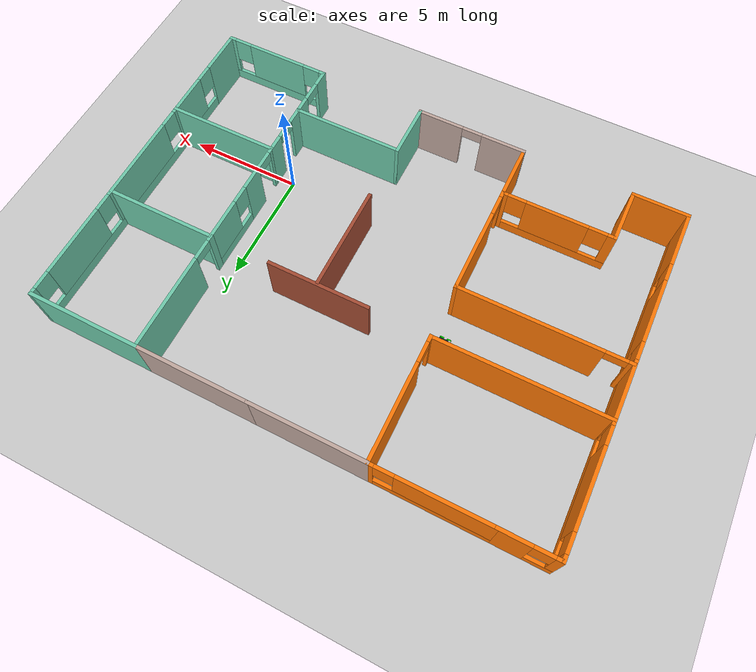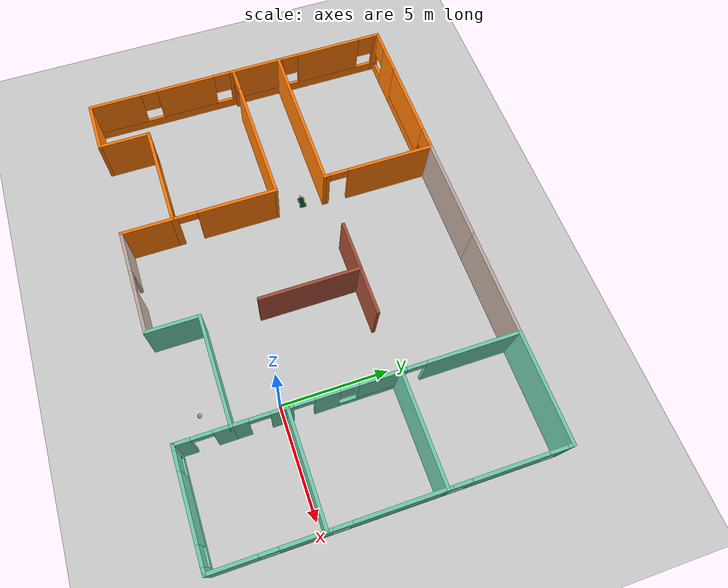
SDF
<sdf version="1.7">
 <world name="default">
  <plugin name="welcome_message" filename="libwelcome_message.so"/>
  <light name="sun" type="directional">
   <pose>0 0 10 0 -0 0</pose>
   <diffuse>0.8 0.8 0.8 1</diffuse>
   <specular>0.2 0.2 0.2 1</specular>
   <attenuation>
    <range>1000</range>
    <constant>0.9</constant>
    <linear>0.01</linear>
    <quadratic>0.001</quadratic>
   </attenuation>
   <direction>-0.5 0.1 -0.9</direction>
   <spot><inner_angle>0</inner_angle><outer_angle>0</outer_angle><falloff>0</falloff></spot>
  </light>
  <model name="ground_plane">
   <static>1</static>
   <link name="link">
    <collision name="collision">
     <geometry><plane><normal>0 0 1</normal><size>100 100</size></plane></geometry>
     <surface>
      <contact><collide_bitmask>65535</collide_bitmask></contact>
      <friction><ode><mu>100</mu><mu2>50</mu2></ode></friction>
     </surface>
    </collision>
    <visual name="visual">
     <cast_shadows>0</cast_shadows>
     <geometry><plane><normal>0 0 1</normal><size>100 100</size></plane></geometry>
     <material>
      <script><uri>file://media/materials/scripts/gazebo.material</uri><name>Gazebo/Grey</name></script>
     </material>
    </visual>
   </link>
  </model>
  <gravity>0 0 -9.8</gravity>
  <magnetic_field>6e-06 2.3e-05 -4.2e-05</magnetic_field>
  <atmosphere type="adiabatic"/>
  <physics name="default_physics" default="0" type="ode">
   <max_step_size>0.001</max_step_size>
   <real_time_factor>1</real_time_factor>
   <real_time_update_rate>1000</real_time_update_rate>
  </physics>
  <scene><ambient>0.4 0.4 0.4 1</ambient><background>0.7 0.7 0.7 1</background><shadows>1</shadows></scene>
  <spherical_coordinates>
   <surface_model>EARTH_WGS84</surface_model>
   <latitude_deg>0</latitude_deg>
   <longitude_deg>0</longitude_deg>
   <elevation>0</elevation>
   <heading_deg>0</heading_deg>
  </spherical_coordinates>
  <model name="World_1">
   <pose>-5.29578 2.9031 0 0 -0 0</pose>
   <link name="Wall_10">
    <pose>6.025 -3.9 0 0 -0 1.5708</pose>
    <visual name="Wall_10_Visual_0">
     <pose>-0.849577 0 1.25 0 -0 0</pose>
     <geometry><box><size>0.800846 0.15 2.5</size></box></geometry>
     <material>
      <script><uri>file://media/materials/scripts/gazebo.material</uri><name>Gazebo/Grey</name></script>
      <ambient>0.435294 0.796078 0.67451 1</ambient>
     </material>
     <meta><layer>0</layer></meta>
    </visual>
    <collision name="Wall_10_Collision_0">
     <geometry><box><size>0.800846 0.15 2.5</size></box></geometry>
     <pose>-0.849577 0 1.25 0 -0 0</pose>
    </collision>
    <visual name="Wall_10_Visual_1">
     <pose>0.850423 0 1.25 0 -0 0</pose>
     <geometry><box><size>0.799154 0.15 2.5</size></box></geometry>
     <material>
      <script><uri>file://media/materials/scripts/gazebo.material</uri><name>Gazebo/Grey</name></script>
      <ambient>0.435294 0.796078 0.67451 1</ambient>
     </material>
     <meta><layer>0</layer></meta>
    </visual>
    <collision name="Wall_10_Collision_1">
     <geometry><box><size>0.799154 0.15 2.5</size></box></geometry>
     <pose>0.850423 0 1.25 0 -0 0</pose>
    </collision>
    <visual name="Wall_10_Visual_2">
     <pose>0.000846 0 2.25 0 -0 0</pose>
     <geometry><box><size>0.9 0.15 0.5</size></box></geometry>
     <material>
      <script><uri>file://media/materials/scripts/gazebo.material</uri><name>Gazebo/Grey</name></script>
      <ambient>0.435294 0.796078 0.67451 1</ambient>
     </material>
     <meta><layer>0</layer></meta>
    </visual>
    <collision name="Wall_10_Collision_2">
     <geometry><box><size>0.9 0.15 0.5</size></box></geometry>
     <pose>0.000846 0 2.25 0 -0 0</pose>
    </collision>
   </link>
   <link name="Wall_11">
    <collision name="Wall_11_Collision">
     <geometry><box><size>5 0.15 2.5</size></box></geometry>
     <pose>0 0 1.25 0 -0 0</pose>
    </collision>
    <visual name="Wall_11_Visual">
     <pose>0 0 1.25 0 -0 0</pose>
     <geometry><box><size>5 0.15 2.5</size></box></geometry>
     <material>
      <script><uri>file://media/materials/scripts/gazebo.material</uri><name>Gazebo/Grey</name></script>
      <ambient>0.435294 0.796078 0.67451 1</ambient>
     </material>
     <meta><layer>0</layer></meta>
    </visual>
    <pose>8.45 -2.725 0 0 -0 0</pose>
   </link>
   <link name="Wall_13">
    <pose>6.025 -0.3 0 0 -0 1.5708</pose>
    <visual name="Wall_13_Visual_0">
     <pose>-2.34458 0 1.25 0 -0 0</pose>
     <geometry><box><size>0.310846 0.15 2.5</size></box></geometry>
     <material>
      <script><uri>file://media/materials/scripts/gazebo.material</uri><name>Gazebo/Grey</name></script>
      <ambient>0.435294 0.796078 0.67451 1</ambient>
     </material>
     <meta><layer>0</layer></meta>
    </visual>
    <collision name="Wall_13_Collision_0">
     <geometry><box><size>0.310846 0.15 2.5</size></box></geometry>
     <pose>-2.34458 0 1.25 0 -0 0</pose>
    </collision>
    <visual name="Wall_13_Visual_1">
     <pose>-0.744154 0 1.25 0 -0 0</pose>
     <geometry><box><size>1.09 0.15 2.5</size></box></geometry>
     <material>
      <script><uri>file://media/materials/scripts/gazebo.material</uri><name>Gazebo/Grey</name></script>
      <ambient>0.435294 0.796078 0.67451 1</ambient>
     </material>
     <meta><layer>0</layer></meta>
    </visual>
    <collision name="Wall_13_Collision_1">
     <geometry><box><size>1.09 0.15 2.5</size></box></geometry>
     <pose>-0.744154 0 1.25 0 -0 0</pose>
    </collision>
    <visual name="Wall_13_Visual_2">
     <pose>1.15042 0 0.25 0 -0 0</pose>
     <geometry><box><size>2.69915 0.15 0.5</size></box></geometry>
     <material>
      <script><uri>file://media/materials/scripts/gazebo.material</uri><name>Gazebo/Grey</name></script>
      <ambient>0.435294 0.796078 0.67451 1</ambient>
     </material>
     <meta><layer>0</layer></meta>
    </visual>
    <collision name="Wall_13_Collision_2">
     <geometry><box><size>2.69915 0.15 0.5</size></box></geometry>
     <pose>1.15042 0 0.25 0 -0 0</pose>
    </collision>
    <visual name="Wall_13_Visual_3">
     <pose>1.55042 0 1.5 0 -0 0</pose>
     <geometry><box><size>1.89915 0.15 2</size></box></geometry>
     <material>
      <script><uri>file://media/materials/scripts/gazebo.material</uri><name>Gazebo/Grey</name></script>
      <ambient>0.435294 0.796078 0.67451 1</ambient>
     </material>
     <meta><layer>0</layer></meta>
    </visual>
    <collision name="Wall_13_Collision_3">
     <geometry><box><size>1.89915 0.15 2</size></box></geometry>
     <pose>1.55042 0 1.5 0 -0 0</pose>
    </collision>
    <visual name="Wall_13_Visual_4">
     <pose>0.200846 0 1.9 0 -0 0</pose>
     <geometry><box><size>0.8 0.15 1.2</size></box></geometry>
     <material>
      <script><uri>file://media/materials/scripts/gazebo.material</uri><name>Gazebo/Grey</name></script>
      <ambient>0.435294 0.796078 0.67451 1</ambient>
     </material>
     <meta><layer>0</layer></meta>
    </visual>
    <collision name="Wall_13_Collision_4">
     <geometry><box><size>0.8 0.15 1.2</size></box></geometry>
     <pose>0.200846 0 1.9 0 -0 0</pose>
    </collision>
    <visual name="Wall_13_Visual_5">
     <pose>-1.73915 0 2.25 0 -0 0</pose>
     <geometry><box><size>0.9 0.15 0.5</size></box></geometry>
     <material>
      <script><uri>file://media/materials/scripts/gazebo.material</uri><name>Gazebo/Grey</name></script>
      <ambient>0.435294 0.796078 0.67451 1</ambient>
     </material>
     <meta><layer>0</layer></meta>
    </visual>
    <collision name="Wall_13_Collision_5">
     <geometry><box><size>0.9 0.15 0.5</size></box></geometry>
     <pose>-1.73915 0 2.25 0 -0 0</pose>
    </collision>
   </link>
   <link name="Wall_14">
    <collision name="Wall_14_Collision">
     <geometry><box><size>5 0.15 2.5</size></box></geometry>
     <pose>0 0 1.25 0 -0 0</pose>
    </collision>
    <visual name="Wall_14_Visual">
     <pose>0 0 1.25 0 -0 0</pose>
     <geometry><box><size>5 0.15 2.5</size></box></geometry>
     <material>
      <script><uri>file://media/materials/scripts/gazebo.material</uri><name>Gazebo/Grey</name></script>
      <ambient>0.435294 0.796078 0.67451 1</ambient>
     </material>
     <meta><layer>0</layer></meta>
    </visual>
    <pose>8.45 2.125 0 0 -0 0</pose>
   </link>
   <link name="Wall_16">
    <collision name="Wall_16_Collision">
     <geometry><box><size>5 0.15 2.5</size></box></geometry>
     <pose>0 0 1.25 0 -0 0</pose>
    </collision>
    <visual name="Wall_16_Visual">
     <pose>0 0 1.25 0 -0 0</pose>
     <geometry><box><size>5 0.15 2.5</size></box></geometry>
     <material>
      <script><uri>file://media/materials/scripts/gazebo.material</uri><name>Gazebo/Grey</name></script>
      <ambient>0.435294 0.796078 0.67451 1</ambient>
     </material>
     <meta><layer>0</layer></meta>
    </visual>
    <pose>8.45 7.425 0 0 -0 3.14159</pose>
   </link>
   <link name="Wall_17">
    <pose>6.025 4.775 0 0 0 -1.5708</pose>
    <visual name="Wall_17_Visual_0">
     <pose>-0.605423 0 1.25 0 -0 0</pose>
     <geometry><box><size>4.23915 0.15 2.5</size></box></geometry>
     <material>
      <script><uri>file://media/materials/scripts/gazebo.material</uri><name>Gazebo/Grey</name></script>
      <ambient>0.435294 0.796078 0.67451 1</ambient>
     </material>
     <meta><layer>0</layer></meta>
    </visual>
    <collision name="Wall_17_Collision_0">
     <geometry><box><size>4.23915 0.15 2.5</size></box></geometry>
     <pose>-0.605423 0 1.25 0 -0 0</pose>
    </collision>
    <visual name="Wall_17_Visual_1">
     <pose>2.56958 0 1.25 0 -0 0</pose>
     <geometry><box><size>0.310846 0.15 2.5</size></box></geometry>
     <material>
      <script><uri>file://media/materials/scripts/gazebo.material</uri><name>Gazebo/Grey</name></script>
      <ambient>0.435294 0.796078 0.67451 1</ambient>
     </material>
     <meta><layer>0</layer></meta>
    </visual>
    <collision name="Wall_17_Collision_1">
     <geometry><box><size>0.310846 0.15 2.5</size></box></geometry>
     <pose>2.56958 0 1.25 0 -0 0</pose>
    </collision>
    <visual name="Wall_17_Visual_2">
     <pose>1.96415 0 2.25 0 -0 0</pose>
     <geometry><box><size>0.9 0.15 0.5</size></box></geometry>
     <material>
      <script><uri>file://media/materials/scripts/gazebo.material</uri><name>Gazebo/Grey</name></script>
      <ambient>0.435294 0.796078 0.67451 1</ambient>
     </material>
     <meta><layer>0</layer></meta>
    </visual>
    <collision name="Wall_17_Collision_2">
     <geometry><box><size>0.9 0.15 0.5</size></box></geometry>
     <pose>1.96415 0 2.25 0 -0 0</pose>
    </collision>
   </link>
   <link name="Wall_19">
    <collision name="Wall_19_Collision">
     <geometry><box><size>2.5 0.15 2.5</size></box></geometry>
     <pose>0 0 1.25 0 -0 0</pose>
    </collision>
    <visual name="Wall_19_Visual">
     <pose>0 0 1.25 0 -0 0</pose>
     <geometry><box><size>2.5 0.15 2.5</size></box></geometry>
     <material>
      <script><uri>file://media/materials/scripts/gazebo.material</uri><name>Gazebo/Grey</name></script>
      <ambient>0.996078 0.47451 0.0196078 1</ambient>
     </material>
     <meta><layer>0</layer></meta>
    </visual>
    <pose>-3.675 -6.25 0 0 -0 1.5708</pose>
   </link>
   <link name="Wall_2">
    <pose>-1.25 -7.425 0 0 -0 0</pose>
    <visual name="Wall_2_Visual_0">
     <pose>-1.5042 0 1.25 0 -0 0</pose>
     <geometry><box><size>1.99161 0.15 2.5</size></box></geometry>
     <material>
      <script><uri>file://media/materials/scripts/gazebo.material</uri><name>Gazebo/Grey</name></script>
      <ambient>0.760784 0.662745 0.627451 1</ambient>
     </material>
     <meta><layer>0</layer></meta>
    </visual>
    <collision name="Wall_2_Collision_0">
     <geometry><box><size>1.99161 0.15 2.5</size></box></geometry>
     <pose>-1.5042 0 1.25 0 -0 0</pose>
    </collision>
    <visual name="Wall_2_Visual_1">
     <pose>1.4458 0 1.25 0 -0 0</pose>
     <geometry><box><size>2.10839 0.15 2.5</size></box></geometry>
     <material>
      <script><uri>file://media/materials/scripts/gazebo.material</uri><name>Gazebo/Grey</name></script>
      <ambient>0.760784 0.662745 0.627451 1</ambient>
     </material>
     <meta><layer>0</layer></meta>
    </visual>
    <collision name="Wall_2_Collision_1">
     <geometry><box><size>2.10839 0.15 2.5</size></box></geometry>
     <pose>1.4458 0 1.25 0 -0 0</pose>
    </collision>
    <visual name="Wall_2_Visual_2">
     <pose>-0.058393 0 2.25 0 -0 0</pose>
     <geometry><box><size>0.9 0.15 0.5</size></box></geometry>
     <material>
      <script><uri>file://media/materials/scripts/gazebo.material</uri><name>Gazebo/Grey</name></script>
      <ambient>0.760784 0.662745 0.627451 1</ambient>
     </material>
     <meta><layer>0</layer></meta>
    </visual>
    <collision name="Wall_2_Collision_2">
     <geometry><box><size>0.9 0.15 0.5</size></box></geometry>
     <pose>-0.058393 0 2.25 0 -0 0</pose>
    </collision>
   </link>
   <link name="Wall_21">
    <pose>-6.1 -5.075 0 0 -0 3.14159</pose>
    <visual name="Wall_21_Visual_0">
     <pose>-2.34529 0 1.25 0 -0 0</pose>
     <geometry><box><size>0.309417 0.15 2.5</size></box></geometry>
     <material>
      <script><uri>file://media/materials/scripts/gazebo.material</uri><name>Gazebo/Grey</name></script>
      <ambient>0.996078 0.47451 0.0196078 1</ambient>
     </material>
     <meta><layer>0</layer></meta>
    </visual>
    <collision name="Wall_21_Collision_0">
     <geometry><box><size>0.309417 0.15 2.5</size></box></geometry>
     <pose>-2.34529 0 1.25 0 -0 0</pose>
    </collision>
    <visual name="Wall_21_Visual_1">
     <pose>0.154709 0 0.25 0 -0 0</pose>
     <geometry><box><size>4.69058 0.15 0.5</size></box></geometry>
     <material>
      <script><uri>file://media/materials/scripts/gazebo.material</uri><name>Gazebo/Grey</name></script>
      <ambient>0.996078 0.47451 0.0196078 1</ambient>
     </material>
     <meta><layer>0</layer></meta>
    </visual>
    <collision name="Wall_21_Collision_1">
     <geometry><box><size>4.69058 0.15 0.5</size></box></geometry>
     <pose>0.154709 0 0.25 0 -0 0</pose>
    </collision>
    <visual name="Wall_21_Visual_2">
     <pose>-0.040702 0 1.5 0 -0 0</pose>
     <geometry><box><size>2.69976 0.15 2</size></box></geometry>
     <material>
      <script><uri>file://media/materials/scripts/gazebo.material</uri><name>Gazebo/Grey</name></script>
      <ambient>0.996078 0.47451 0.0196078 1</ambient>
     </material>
     <meta><layer>0</layer></meta>
    </visual>
    <collision name="Wall_21_Collision_2">
     <geometry><box><size>2.69976 0.15 2</size></box></geometry>
     <pose>-0.040702 0 1.5 0 -0 0</pose>
    </collision>
    <visual name="Wall_21_Visual_3">
     <pose>2.30459 0 1.5 0 -0 0</pose>
     <geometry><box><size>0.390821 0.15 2</size></box></geometry>
     <material>
      <script><uri>file://media/materials/scripts/gazebo.material</uri><name>Gazebo/Grey</name></script>
      <ambient>0.996078 0.47451 0.0196078 1</ambient>
     </material>
     <meta><layer>0</layer></meta>
    </visual>
    <collision name="Wall_21_Collision_3">
     <geometry><box><size>0.390821 0.15 2</size></box></geometry>
     <pose>2.30459 0 1.5 0 -0 0</pose>
    </collision>
    <visual name="Wall_21_Visual_4">
     <pose>-1.79058 0 1.9 0 -0 0</pose>
     <geometry><box><size>0.8 0.15 1.2</size></box></geometry>
     <material>
      <script><uri>file://media/materials/scripts/gazebo.material</uri><name>Gazebo/Grey</name></script>
      <ambient>0.996078 0.47451 0.0196078 1</ambient>
     </material>
     <meta><layer>0</layer></meta>
    </visual>
    <collision name="Wall_21_Collision_4">
     <geometry><box><size>0.8 0.15 1.2</size></box></geometry>
     <pose>-1.79058 0 1.9 0 -0 0</pose>
    </collision>
    <visual name="Wall_21_Visual_5">
     <pose>1.70918 0 1.9 0 -0 0</pose>
     <geometry><box><size>0.8 0.15 1.2</size></box></geometry>
     <material>
      <script><uri>file://media/materials/scripts/gazebo.material</uri><name>Gazebo/Grey</name></script>
      <ambient>0.996078 0.47451 0.0196078 1</ambient>
     </material>
     <meta><layer>0</layer></meta>
    </visual>
    <collision name="Wall_21_Collision_5">
     <geometry><box><size>0.8 0.15 1.2</size></box></geometry>
     <pose>1.70918 0 1.9 0 -0 0</pose>
    </collision>
   </link>
   <link name="Wall_3">
    <collision name="Wall_3_Collision">
     <geometry><box><size>2.5 0.15 2.5</size></box></geometry>
     <pose>0 0 1.25 0 -0 0</pose>
    </collision>
    <visual name="Wall_3_Visual">
     <pose>0 0 1.25 0 -0 0</pose>
     <geometry><box><size>2.5 0.15 2.5</size></box></geometry>
     <material>
      <script><uri>file://media/materials/scripts/gazebo.material</uri><name>Gazebo/Grey</name></script>
      <ambient>0.435294 0.796078 0.67451 1</ambient>
     </material>
     <meta><layer>0</layer></meta>
    </visual>
    <pose>1.175 -6.25 0 0 -0 1.5708</pose>
   </link>
   <link name="Wall_34">
    <collision name="Wall_34_Collision">
     <geometry><box><size>2.5 0.15 2.5</size></box></geometry>
     <pose>0 0 1.25 0 -0 0</pose>
    </collision>
    <visual name="Wall_34_Visual">
     <pose>0 0 1.25 0 -0 0</pose>
     <geometry><box><size>2.5 0.15 2.5</size></box></geometry>
     <material>
      <script><uri>file://media/materials/scripts/gazebo.material</uri><name>Gazebo/Grey</name></script>
      <ambient>0.996078 0.47451 0.0196078 1</ambient>
     </material>
     <meta><layer>0</layer></meta>
    </visual>
    <pose>-8.525 -6.25 0 0 0 -1.5708</pose>
   </link>
   <link name="Wall_38">
    <collision name="Wall_38_Collision">
     <geometry><box><size>5 0.15 2.5</size></box></geometry>
     <pose>0 0 1.25 0 -0 0</pose>
    </collision>
    <visual name="Wall_38_Visual">
     <pose>0 0 1.25 0 -0 0</pose>
     <geometry><box><size>5 0.15 2.5</size></box></geometry>
     <material>
      <script><uri>file://media/materials/scripts/gazebo.material</uri><name>Gazebo/Grey</name></script>
      <ambient>0.760784 0.662745 0.627451 1</ambient>
     </material>
     <meta><layer>0</layer></meta>
    </visual>
    <pose>3.6 7.425 0 0 -0 3.14159</pose>
   </link>
   <link name="Wall_39">
    <collision name="Wall_39_Collision">
     <geometry><box><size>5 0.15 2.5</size></box></geometry>
     <pose>0 0 1.25 0 -0 0</pose>
    </collision>
    <visual name="Wall_39_Visual">
     <pose>0 0 1.25 0 -0 0</pose>
     <geometry><box><size>5 0.15 2.5</size></box></geometry>
     <material>
      <script><uri>file://media/materials/scripts/gazebo.material</uri><name>Gazebo/Grey</name></script>
      <ambient>0.760784 0.662745 0.627451 1</ambient>
     </material>
     <meta><layer>0</layer></meta>
    </visual>
    <pose>-1.25 7.425 0 0 -0 3.14159</pose>
   </link>
   <link name="Wall_4">
    <collision name="Wall_4_Collision">
     <geometry><box><size>5 0.15 2.5</size></box></geometry>
     <pose>0 0 1.25 0 -0 0</pose>
    </collision>
    <visual name="Wall_4_Visual">
     <pose>0 0 1.25 0 -0 0</pose>
     <geometry><box><size>5 0.15 2.5</size></box></geometry>
     <material>
      <script><uri>file://media/materials/scripts/gazebo.material</uri><name>Gazebo/Grey</name></script>
      <ambient>0.435294 0.796078 0.67451 1</ambient>
     </material>
     <meta><layer>0</layer></meta>
    </visual>
    <pose>3.6 -5.075 0 0 -0 0</pose>
   </link>
   <link name="Wall_40">
    <pose>-6.1 7.425 0 0 -0 3.14159</pose>
    <visual name="Wall_40_Visual_0">
     <pose>-2.3458 0 1.25 0 -0 0</pose>
     <geometry><box><size>0.308393 0.15 2.5</size></box></geometry>
     <material>
      <script><uri>file://media/materials/scripts/gazebo.material</uri><name>Gazebo/Grey</name></script>
      <ambient>0.996078 0.47451 0.0196078 1</ambient>
     </material>
     <meta><layer>0</layer></meta>
    </visual>
    <collision name="Wall_40_Collision_0">
     <geometry><box><size>0.308393 0.15 2.5</size></box></geometry>
     <pose>-2.3458 0 1.25 0 -0 0</pose>
    </collision>
    <visual name="Wall_40_Visual_1">
     <pose>0.154197 0 0.25 0 -0 0</pose>
     <geometry><box><size>4.69161 0.15 0.5</size></box></geometry>
     <material>
      <script><uri>file://media/materials/scripts/gazebo.material</uri><name>Gazebo/Grey</name></script>
      <ambient>0.996078 0.47451 0.0196078 1</ambient>
     </material>
     <meta><layer>0</layer></meta>
    </visual>
    <collision name="Wall_40_Collision_1">
     <geometry><box><size>4.69161 0.15 0.5</size></box></geometry>
     <pose>0.154197 0 0.25 0 -0 0</pose>
    </collision>
    <visual name="Wall_40_Visual_2">
     <pose>0.554197 0 1.5 0 -0 0</pose>
     <geometry><box><size>3.89161 0.15 2</size></box></geometry>
     <material>
      <script><uri>file://media/materials/scripts/gazebo.material</uri><name>Gazebo/Grey</name></script>
      <ambient>0.996078 0.47451 0.0196078 1</ambient>
     </material>
     <meta><layer>0</layer></meta>
    </visual>
    <collision name="Wall_40_Collision_2">
     <geometry><box><size>3.89161 0.15 2</size></box></geometry>
     <pose>0.554197 0 1.5 0 -0 0</pose>
    </collision>
    <visual name="Wall_40_Visual_3">
     <pose>-1.79161 0 1.9 0 -0 0</pose>
     <geometry><box><size>0.8 0.15 1.2</size></box></geometry>
     <material>
      <script><uri>file://media/materials/scripts/gazebo.material</uri><name>Gazebo/Grey</name></script>
      <ambient>0.996078 0.47451 0.0196078 1</ambient>
     </material>
     <meta><layer>0</layer></meta>
    </visual>
    <collision name="Wall_40_Collision_3">
     <geometry><box><size>0.8 0.15 1.2</size></box></geometry>
     <pose>-1.79161 0 1.9 0 -0 0</pose>
    </collision>
   </link>
   <link name="Wall_43">
    <collision name="Wall_43_Collision">
     <geometry><box><size>2.5 0.15 2.5</size></box></geometry>
     <pose>0 0 1.25 0 -0 0</pose>
    </collision>
    <visual name="Wall_43_Visual">
     <pose>0 0 1.25 0 -0 0</pose>
     <geometry><box><size>2.5 0.15 2.5</size></box></geometry>
     <material>
      <script><uri>file://media/materials/scripts/gazebo.material</uri><name>Gazebo/Grey</name></script>
      <ambient>0.996078 0.47451 0.0196078 1</ambient>
     </material>
     <meta><layer>0</layer></meta>
    </visual>
    <pose>-9.7 -7.425 0 0 -0 3.14159</pose>
   </link>
   <link name="Wall_45">
    <pose>-9.7 7.425 0 0 -0 3.14159</pose>
    <visual name="Wall_45_Visual_0">
     <pose>-0.560804 0 1.25 0 -0 0</pose>
     <geometry><box><size>1.37839 0.15 2.5</size></box></geometry>
     <material>
      <script><uri>file://media/materials/scripts/gazebo.material</uri><name>Gazebo/Grey</name></script>
      <ambient>0.996078 0.47451 0.0196078 1</ambient>
     </material>
     <meta><layer>0</layer></meta>
    </visual>
    <collision name="Wall_45_Collision_0">
     <geometry><box><size>1.37839 0.15 2.5</size></box></geometry>
     <pose>-0.560804 0 1.25 0 -0 0</pose>
    </collision>
    <visual name="Wall_45_Visual_1">
     <pose>0.689196 0 0.25 0 -0 0</pose>
     <geometry><box><size>1.12161 0.15 0.5</size></box></geometry>
     <material>
      <script><uri>file://media/materials/scripts/gazebo.material</uri><name>Gazebo/Grey</name></script>
      <ambient>0.996078 0.47451 0.0196078 1</ambient>
     </material>
     <meta><layer>0</layer></meta>
    </visual>
    <collision name="Wall_45_Collision_1">
     <geometry><box><size>1.12161 0.15 0.5</size></box></geometry>
     <pose>0.689196 0 0.25 0 -0 0</pose>
    </collision>
    <visual name="Wall_45_Visual_2">
     <pose>1.0892 0 1.5 0 -0 0</pose>
     <geometry><box><size>0.321607 0.15 2</size></box></geometry>
     <material>
      <script><uri>file://media/materials/scripts/gazebo.material</uri><name>Gazebo/Grey</name></script>
      <ambient>0.996078 0.47451 0.0196078 1</ambient>
     </material>
     <meta><layer>0</layer></meta>
    </visual>
    <collision name="Wall_45_Collision_2">
     <geometry><box><size>0.321607 0.15 2</size></box></geometry>
     <pose>1.0892 0 1.5 0 -0 0</pose>
    </collision>
    <visual name="Wall_45_Visual_3">
     <pose>0.528393 0 1.9 0 -0 0</pose>
     <geometry><box><size>0.8 0.15 1.2</size></box></geometry>
     <material>
      <script><uri>file://media/materials/scripts/gazebo.material</uri><name>Gazebo/Grey</name></script>
      <ambient>0.996078 0.47451 0.0196078 1</ambient>
     </material>
     <meta><layer>0</layer></meta>
    </visual>
    <collision name="Wall_45_Collision_3">
     <geometry><box><size>0.8 0.15 1.2</size></box></geometry>
     <pose>0.528393 0 1.9 0 -0 0</pose>
    </collision>
   </link>
   <link name="Wall_46">
    <pose>-10.875 0 0 0 0 -1.5708</pose>
    <visual name="Wall_46_Visual_0">
     <pose>-7.34042 0 1.25 0 -0 0</pose>
     <geometry><box><size>0.319154 0.15 2.5</size></box></geometry>
     <material>
      <script><uri>file://media/materials/scripts/gazebo.material</uri><name>Gazebo/Grey</name></script>
      <ambient>0.996078 0.47451 0.0196078 1</ambient>
     </material>
     <meta><layer>0</layer></meta>
    </visual>
    <collision name="Wall_46_Collision_0">
     <geometry><box><size>0.319154 0.15 2.5</size></box></geometry>
     <pose>-7.34042 0 1.25 0 -0 0</pose>
    </collision>
    <visual name="Wall_46_Visual_1">
     <pose>0.159577 0 0.25 0 -0 0</pose>
     <geometry><box><size>14.6808 0.15 0.5</size></box></geometry>
     <material>
      <script><uri>file://media/materials/scripts/gazebo.material</uri><name>Gazebo/Grey</name></script>
      <ambient>0.996078 0.47451 0.0196078 1</ambient>
     </material>
     <meta><layer>0</layer></meta>
    </visual>
    <collision name="Wall_46_Collision_1">
     <geometry><box><size>14.6808 0.15 0.5</size></box></geometry>
     <pose>0.159577 0 0.25 0 -0 0</pose>
    </collision>
    <visual name="Wall_46_Visual_2">
     <pose>-4.75585 0 1.5 0 -0 0</pose>
     <geometry><box><size>3.25 0.15 2</size></box></geometry>
     <material>
      <script><uri>file://media/materials/scripts/gazebo.material</uri><name>Gazebo/Grey</name></script>
      <ambient>0.996078 0.47451 0.0196078 1</ambient>
     </material>
     <meta><layer>0</layer></meta>
    </visual>
    <collision name="Wall_46_Collision_2">
     <geometry><box><size>3.25 0.15 2</size></box></geometry>
     <pose>-4.75585 0 1.5 0 -0 0</pose>
    </collision>
    <visual name="Wall_46_Visual_3">
     <pose>-0.940846 0 1.5 0 -0 0</pose>
     <geometry><box><size>2.78 0.15 2</size></box></geometry>
     <material>
      <script><uri>file://media/materials/scripts/gazebo.material</uri><name>Gazebo/Grey</name></script>
      <ambient>0.996078 0.47451 0.0196078 1</ambient>
     </material>
     <meta><layer>0</layer></meta>
    </visual>
    <collision name="Wall_46_Collision_3">
     <geometry><box><size>2.78 0.15 2</size></box></geometry>
     <pose>-0.940846 0 1.5 0 -0 0</pose>
    </collision>
    <visual name="Wall_46_Visual_4">
     <pose>2.68915 0 1.5 0 -0 0</pose>
     <geometry><box><size>2.88 0.15 2</size></box></geometry>
     <material>
      <script><uri>file://media/materials/scripts/gazebo.material</uri><name>Gazebo/Grey</name></script>
      <ambient>0.996078 0.47451 0.0196078 1</ambient>
     </material>
     <meta><layer>0</layer></meta>
    </visual>
    <collision name="Wall_46_Collision_4">
     <geometry><box><size>2.88 0.15 2</size></box></geometry>
     <pose>2.68915 0 1.5 0 -0 0</pose>
    </collision>
    <visual name="Wall_46_Visual_5">
     <pose>6.21458 0 1.5 0 -0 0</pose>
     <geometry><box><size>2.57085 0.15 2</size></box></geometry>
     <material>
      <script><uri>file://media/materials/scripts/gazebo.material</uri><name>Gazebo/Grey</name></script>
      <ambient>0.996078 0.47451 0.0196078 1</ambient>
     </material>
     <meta><layer>0</layer></meta>
    </visual>
    <collision name="Wall_46_Collision_5">
     <geometry><box><size>2.57085 0.15 2</size></box></geometry>
     <pose>6.21458 0 1.5 0 -0 0</pose>
    </collision>
    <visual name="Wall_46_Visual_6">
     <pose>-6.78085 0 1.9 0 -0 0</pose>
     <geometry><box><size>0.8 0.15 1.2</size></box></geometry>
     <material>
      <script><uri>file://media/materials/scripts/gazebo.material</uri><name>Gazebo/Grey</name></script>
      <ambient>0.996078 0.47451 0.0196078 1</ambient>
     </material>
     <meta><layer>0</layer></meta>
    </visual>
    <collision name="Wall_46_Collision_6">
     <geometry><box><size>0.8 0.15 1.2</size></box></geometry>
     <pose>-6.78085 0 1.9 0 -0 0</pose>
    </collision>
    <visual name="Wall_46_Visual_7">
     <pose>-2.73085 0 1.9 0 -0 0</pose>
     <geometry><box><size>0.8 0.15 1.2</size></box></geometry>
     <material>
      <script><uri>file://media/materials/scripts/gazebo.material</uri><name>Gazebo/Grey</name></script>
      <ambient>0.996078 0.47451 0.0196078 1</ambient>
     </material>
     <meta><layer>0</layer></meta>
    </visual>
    <collision name="Wall_46_Collision_7">
     <geometry><box><size>0.8 0.15 1.2</size></box></geometry>
     <pose>-2.73085 0 1.9 0 -0 0</pose>
    </collision>
    <visual name="Wall_46_Visual_8">
     <pose>0.849154 0 1.9 0 -0 0</pose>
     <geometry><box><size>0.8 0.15 1.2</size></box></geometry>
     <material>
      <script><uri>file://media/materials/scripts/gazebo.material</uri><name>Gazebo/Grey</name></script>
      <ambient>0.996078 0.47451 0.0196078 1</ambient>
     </material>
     <meta><layer>0</layer></meta>
    </visual>
    <collision name="Wall_46_Collision_8">
     <geometry><box><size>0.8 0.15 1.2</size></box></geometry>
     <pose>0.849154 0 1.9 0 -0 0</pose>
    </collision>
    <visual name="Wall_46_Visual_9">
     <pose>4.52915 0 1.9 0 -0 0</pose>
     <geometry><box><size>0.8 0.15 1.2</size></box></geometry>
     <material>
      <script><uri>file://media/materials/scripts/gazebo.material</uri><name>Gazebo/Grey</name></script>
      <ambient>0.996078 0.47451 0.0196078 1</ambient>
     </material>
     <meta><layer>0</layer></meta>
    </visual>
    <collision name="Wall_46_Collision_9">
     <geometry><box><size>0.8 0.15 1.2</size></box></geometry>
     <pose>4.52915 0 1.9 0 -0 0</pose>
    </collision>
   </link>
   <link name="Wall_48">
    <pose>-3.675 -2.65 0 0 -0 1.5708</pose>
    <visual name="Wall_48_Visual_0">
     <pose>-2.34458 0 1.25 0 -0 0</pose>
     <geometry><box><size>0.310846 0.15 2.5</size></box></geometry>
     <material>
      <script><uri>file://media/materials/scripts/gazebo.material</uri><name>Gazebo/Grey</name></script>
      <ambient>0.996078 0.47451 0.0196078 1</ambient>
     </material>
     <meta><layer>0</layer></meta>
    </visual>
    <collision name="Wall_48_Collision_0">
     <geometry><box><size>0.310846 0.15 2.5</size></box></geometry>
     <pose>-2.34458 0 1.25 0 -0 0</pose>
    </collision>
    <visual name="Wall_48_Visual_1">
     <pose>0.605423 0 1.25 0 -0 0</pose>
     <geometry><box><size>3.78915 0.15 2.5</size></box></geometry>
     <material>
      <script><uri>file://media/materials/scripts/gazebo.material</uri><name>Gazebo/Grey</name></script>
      <ambient>0.996078 0.47451 0.0196078 1</ambient>
     </material>
     <meta><layer>0</layer></meta>
    </visual>
    <collision name="Wall_48_Collision_1">
     <geometry><box><size>3.78915 0.15 2.5</size></box></geometry>
     <pose>0.605423 0 1.25 0 -0 0</pose>
    </collision>
    <visual name="Wall_48_Visual_2">
     <pose>-1.73915 0 2.25 0 -0 0</pose>
     <geometry><box><size>0.9 0.15 0.5</size></box></geometry>
     <material>
      <script><uri>file://media/materials/scripts/gazebo.material</uri><name>Gazebo/Grey</name></script>
      <ambient>0.996078 0.47451 0.0196078 1</ambient>
     </material>
     <meta><layer>0</layer></meta>
    </visual>
    <collision name="Wall_48_Collision_2">
     <geometry><box><size>0.9 0.15 0.5</size></box></geometry>
     <pose>-1.73915 0 2.25 0 -0 0</pose>
    </collision>
   </link>
   <link name="Wall_5">
    <pose>6.025 -6.25 0 0 0 -1.5708</pose>
    <visual name="Wall_5_Visual_0">
     <pose>-0.845423 0 1.25 0 -0 0</pose>
     <geometry><box><size>0.809154 0.15 2.5</size></box></geometry>
     <material>
      <script><uri>file://media/materials/scripts/gazebo.material</uri><name>Gazebo/Grey</name></script>
      <ambient>0.435294 0.796078 0.67451 1</ambient>
     </material>
     <meta><layer>0</layer></meta>
    </visual>
    <collision name="Wall_5_Collision_0">
     <geometry><box><size>0.809154 0.15 2.5</size></box></geometry>
     <pose>-0.845423 0 1.25 0 -0 0</pose>
    </collision>
    <visual name="Wall_5_Visual_1">
     <pose>0.854577 0 1.25 0 -0 0</pose>
     <geometry><box><size>0.790846 0.15 2.5</size></box></geometry>
     <material>
      <script><uri>file://media/materials/scripts/gazebo.material</uri><name>Gazebo/Grey</name></script>
      <ambient>0.435294 0.796078 0.67451 1</ambient>
     </material>
     <meta><layer>0</layer></meta>
    </visual>
    <collision name="Wall_5_Collision_1">
     <geometry><box><size>0.790846 0.15 2.5</size></box></geometry>
     <pose>0.854577 0 1.25 0 -0 0</pose>
    </collision>
    <visual name="Wall_5_Visual_2">
     <pose>0.009154 0 2.25 0 -0 0</pose>
     <geometry><box><size>0.9 0.15 0.5</size></box></geometry>
     <material>
      <script><uri>file://media/materials/scripts/gazebo.material</uri><name>Gazebo/Grey</name></script>
      <ambient>0.435294 0.796078 0.67451 1</ambient>
     </material>
     <meta><layer>0</layer></meta>
    </visual>
    <collision name="Wall_5_Collision_2">
     <geometry><box><size>0.9 0.15 0.5</size></box></geometry>
     <pose>0.009154 0 2.25 0 -0 0</pose>
    </collision>
   </link>
   <link name="Wall_50">
    <pose>-7.275 -0.225 0 0 -0 3.14159</pose>
    <visual name="Wall_50_Visual_0">
     <pose>-0.605803 0 1.25 0 -0 0</pose>
     <geometry><box><size>6.13839 0.15 2.5</size></box></geometry>
     <material>
      <script><uri>file://media/materials/scripts/gazebo.material</uri><name>Gazebo/Grey</name></script>
      <ambient>0.996078 0.47451 0.0196078 1</ambient>
     </material>
     <meta><layer>0</layer></meta>
    </visual>
    <collision name="Wall_50_Collision_0">
     <geometry><box><size>6.13839 0.15 2.5</size></box></geometry>
     <pose>-0.605803 0 1.25 0 -0 0</pose>
    </collision>
    <visual name="Wall_50_Visual_1">
     <pose>3.5192 0 1.25 0 -0 0</pose>
     <geometry><box><size>0.311607 0.15 2.5</size></box></geometry>
     <material>
      <script><uri>file://media/materials/scripts/gazebo.material</uri><name>Gazebo/Grey</name></script>
      <ambient>0.996078 0.47451 0.0196078 1</ambient>
     </material>
     <meta><layer>0</layer></meta>
    </visual>
    <collision name="Wall_50_Collision_1">
     <geometry><box><size>0.311607 0.15 2.5</size></box></geometry>
     <pose>3.5192 0 1.25 0 -0 0</pose>
    </collision>
    <visual name="Wall_50_Visual_2">
     <pose>2.91339 0 2.25 0 -0 0</pose>
     <geometry><box><size>0.9 0.15 0.5</size></box></geometry>
     <material>
      <script><uri>file://media/materials/scripts/gazebo.material</uri><name>Gazebo/Grey</name></script>
      <ambient>0.996078 0.47451 0.0196078 1</ambient>
     </material>
     <meta><layer>0</layer></meta>
    </visual>
    <collision name="Wall_50_Collision_2">
     <geometry><box><size>0.9 0.15 0.5</size></box></geometry>
     <pose>2.91339 0 2.25 0 -0 0</pose>
    </collision>
   </link>
   <link name="Wall_53">
    <pose>-3.675 4.775 0 0 0 -1.5708</pose>
    <visual name="Wall_53_Visual_0">
     <pose>-0.610423 0 1.25 0 -0 0</pose>
     <geometry><box><size>4.22915 0.15 2.5</size></box></geometry>
     <material>
      <script><uri>file://media/materials/scripts/gazebo.material</uri><name>Gazebo/Grey</name></script>
      <ambient>0.996078 0.47451 0.0196078 1</ambient>
     </material>
     <meta><layer>0</layer></meta>
    </visual>
    <collision name="Wall_53_Collision_0">
     <geometry><box><size>4.22915 0.15 2.5</size></box></geometry>
     <pose>-0.610423 0 1.25 0 -0 0</pose>
    </collision>
    <visual name="Wall_53_Visual_1">
     <pose>2.56458 0 1.25 0 -0 0</pose>
     <geometry><box><size>0.320846 0.15 2.5</size></box></geometry>
     <material>
      <script><uri>file://media/materials/scripts/gazebo.material</uri><name>Gazebo/Grey</name></script>
      <ambient>0.996078 0.47451 0.0196078 1</ambient>
     </material>
     <meta><layer>0</layer></meta>
    </visual>
    <collision name="Wall_53_Collision_1">
     <geometry><box><size>0.320846 0.15 2.5</size></box></geometry>
     <pose>2.56458 0 1.25 0 -0 0</pose>
    </collision>
    <visual name="Wall_53_Visual_2">
     <pose>1.95415 0 2.25 0 -0 0</pose>
     <geometry><box><size>0.9 0.15 0.5</size></box></geometry>
     <material>
      <script><uri>file://media/materials/scripts/gazebo.material</uri><name>Gazebo/Grey</name></script>
      <ambient>0.996078 0.47451 0.0196078 1</ambient>
     </material>
     <meta><layer>0</layer></meta>
    </visual>
    <collision name="Wall_53_Collision_2">
     <geometry><box><size>0.9 0.15 0.5</size></box></geometry>
     <pose>1.95415 0 2.25 0 -0 0</pose>
    </collision>
   </link>
   <link name="Wall_55">
    <collision name="Wall_55_Collision">
     <geometry><box><size>7.35 0.15 2.5</size></box></geometry>
     <pose>0 0 1.25 0 -0 0</pose>
    </collision>
    <visual name="Wall_55_Visual">
     <pose>0 0 1.25 0 -0 0</pose>
     <geometry><box><size>7.35 0.15 2.5</size></box></geometry>
     <material>
      <script><uri>file://media/materials/scripts/gazebo.material</uri><name>Gazebo/Grey</name></script>
      <ambient>0.996078 0.47451 0.0196078 1</ambient>
     </material>
     <meta><layer>0</layer></meta>
    </visual>
    <pose>-7.275 2.125 0 0 -0 3.14159</pose>
   </link>
   <link name="Wall_57">
    <collision name="Wall_57_Collision">
     <geometry><box><size>4.5 0.15 2.5</size></box></geometry>
     <pose>0 0 1.25 0 -0 0</pose>
    </collision>
    <visual name="Wall_57_Visual">
     <pose>0 0 1.25 0 -0 0</pose>
     <geometry><box><size>4.5 0.15 2.5</size></box></geometry>
     <material>
      <script><uri>file://media/materials/scripts/gazebo.material</uri><name>Gazebo/Bricks</name></script>
      <ambient>1 1 1 1</ambient>
     </material>
     <meta><layer>0</layer></meta>
    </visual>
    <pose>1.15173 2.11728 0 0 -0 0</pose>
   </link>
   <link name="Wall_59">
    <collision name="Wall_59_Collision">
     <geometry><box><size>4.75 0.15 2.5</size></box></geometry>
     <pose>0 0 1.25 0 -0 0</pose>
    </collision>
    <visual name="Wall_59_Visual">
     <pose>0 0 1.25 0 -0 0</pose>
     <geometry><box><size>4.75 0.15 2.5</size></box></geometry>
     <material>
      <script><uri>file://media/materials/scripts/gazebo.material</uri><name>Gazebo/Bricks</name></script>
      <ambient>1 1 1 1</ambient>
     </material>
     <meta><layer>0</layer></meta>
    </visual>
    <pose>1.20673 -0.182724 0 0 0 -1.5708</pose>
   </link>
   <link name="Wall_6">
    <pose>8.45 -7.425 0 0 -0 0</pose>
    <visual name="Wall_6_Visual_0">
     <pose>-2.3492 0 1.25 0 -0 0</pose>
     <geometry><box><size>0.301607 0.15 2.5</size></box></geometry>
     <material>
      <script><uri>file://media/materials/scripts/gazebo.material</uri><name>Gazebo/Grey</name></script>
      <ambient>0.435294 0.796078 0.67451 1</ambient>
     </material>
     <meta><layer>0</layer></meta>
    </visual>
    <collision name="Wall_6_Collision_0">
     <geometry><box><size>0.301607 0.15 2.5</size></box></geometry>
     <pose>-2.3492 0 1.25 0 -0 0</pose>
    </collision>
    <visual name="Wall_6_Visual_1">
     <pose>0.150803 0 0.25 0 -0 0</pose>
     <geometry><box><size>4.69839 0.15 0.5</size></box></geometry>
     <material>
      <script><uri>file://media/materials/scripts/gazebo.material</uri><name>Gazebo/Grey</name></script>
      <ambient>0.435294 0.796078 0.67451 1</ambient>
     </material>
     <meta><layer>0</layer></meta>
    </visual>
    <collision name="Wall_6_Collision_1">
     <geometry><box><size>4.69839 0.15 0.5</size></box></geometry>
     <pose>0.150803 0 0.25 0 -0 0</pose>
    </collision>
    <visual name="Wall_6_Visual_2">
     <pose>-0.013393 0 1.5 0 -0 0</pose>
     <geometry><box><size>2.77 0.15 2</size></box></geometry>
     <material>
      <script><uri>file://media/materials/scripts/gazebo.material</uri><name>Gazebo/Grey</name></script>
      <ambient>0.435294 0.796078 0.67451 1</ambient>
     </material>
     <meta><layer>0</layer></meta>
    </visual>
    <collision name="Wall_6_Collision_2">
     <geometry><box><size>2.77 0.15 2</size></box></geometry>
     <pose>-0.013393 0 1.5 0 -0 0</pose>
    </collision>
    <visual name="Wall_6_Visual_3">
     <pose>2.3358 0 1.5 0 -0 0</pose>
     <geometry><box><size>0.328393 0.15 2</size></box></geometry>
     <material>
      <script><uri>file://media/materials/scripts/gazebo.material</uri><name>Gazebo/Grey</name></script>
      <ambient>0.435294 0.796078 0.67451 1</ambient>
     </material>
     <meta><layer>0</layer></meta>
    </visual>
    <collision name="Wall_6_Collision_3">
     <geometry><box><size>0.328393 0.15 2</size></box></geometry>
     <pose>2.3358 0 1.5 0 -0 0</pose>
    </collision>
    <visual name="Wall_6_Visual_4">
     <pose>-1.79839 0 1.9 0 -0 0</pose>
     <geometry><box><size>0.8 0.15 1.2</size></box></geometry>
     <material>
      <script><uri>file://media/materials/scripts/gazebo.material</uri><name>Gazebo/Grey</name></script>
      <ambient>0.435294 0.796078 0.67451 1</ambient>
     </material>
     <meta><layer>0</layer></meta>
    </visual>
    <collision name="Wall_6_Collision_4">
     <geometry><box><size>0.8 0.15 1.2</size></box></geometry>
     <pose>-1.79839 0 1.9 0 -0 0</pose>
    </collision>
    <visual name="Wall_6_Visual_5">
     <pose>1.77161 0 1.9 0 -0 0</pose>
     <geometry><box><size>0.8 0.15 1.2</size></box></geometry>
     <material>
      <script><uri>file://media/materials/scripts/gazebo.material</uri><name>Gazebo/Grey</name></script>
      <ambient>0.435294 0.796078 0.67451 1</ambient>
     </material>
     <meta><layer>0</layer></meta>
    </visual>
    <collision name="Wall_6_Collision_5">
     <geometry><box><size>0.8 0.15 1.2</size></box></geometry>
     <pose>1.77161 0 1.9 0 -0 0</pose>
    </collision>
   </link>
   <link name="Wall_8">
    <pose>10.875 0 0 0 -0 1.5708</pose>
    <visual name="Wall_8_Visual_0">
     <pose>-6.44458 0 1.25 0 -0 0</pose>
     <geometry><box><size>2.11085 0.15 2.5</size></box></geometry>
     <material>
      <script><uri>file://media/materials/scripts/gazebo.material</uri><name>Gazebo/Grey</name></script>
      <ambient>0.435294 0.796078 0.67451 1</ambient>
     </material>
     <meta><layer>0</layer></meta>
    </visual>
    <collision name="Wall_8_Collision_0">
     <geometry><box><size>2.11085 0.15 2.5</size></box></geometry>
     <pose>-6.44458 0 1.25 0 -0 0</pose>
    </collision>
    <visual name="Wall_8_Visual_1">
     <pose>1.05542 0 0.25 0 -0 0</pose>
     <geometry><box><size>12.8892 0.15 0.5</size></box></geometry>
     <material>
      <script><uri>file://media/materials/scripts/gazebo.material</uri><name>Gazebo/Grey</name></script>
      <ambient>0.435294 0.796078 0.67451 1</ambient>
     </material>
     <meta><layer>0</layer></meta>
    </visual>
    <collision name="Wall_8_Collision_1">
     <geometry><box><size>12.8892 0.15 0.5</size></box></geometry>
     <pose>1.05542 0 0.25 0 -0 0</pose>
    </collision>
    <visual name="Wall_8_Visual_2">
     <pose>-3.54915 0 1.5 0 -0 0</pose>
     <geometry><box><size>2.08 0.15 2</size></box></geometry>
     <material>
      <script><uri>file://media/materials/scripts/gazebo.material</uri><name>Gazebo/Grey</name></script>
      <ambient>0.435294 0.796078 0.67451 1</ambient>
     </material>
     <meta><layer>0</layer></meta>
    </visual>
    <collision name="Wall_8_Collision_2">
     <geometry><box><size>2.08 0.15 2</size></box></geometry>
     <pose>-3.54915 0 1.5 0 -0 0</pose>
    </collision>
    <visual name="Wall_8_Visual_3">
     <pose>0.315846 0 1.5 0 -0 0</pose>
     <geometry><box><size>4.05 0.15 2</size></box></geometry>
     <material>
      <script><uri>file://media/materials/scripts/gazebo.material</uri><name>Gazebo/Grey</name></script>
      <ambient>0.435294 0.796078 0.67451 1</ambient>
     </material>
     <meta><layer>0</layer></meta>
    </visual>
    <collision name="Wall_8_Collision_3">
     <geometry><box><size>4.05 0.15 2</size></box></geometry>
     <pose>0.315846 0 1.5 0 -0 0</pose>
    </collision>
    <visual name="Wall_8_Visual_4">
     <pose>4.76085 0 1.5 0 -0 0</pose>
     <geometry><box><size>3.24 0.15 2</size></box></geometry>
     <material>
      <script><uri>file://media/materials/scripts/gazebo.material</uri><name>Gazebo/Grey</name></script>
      <ambient>0.435294 0.796078 0.67451 1</ambient>
     </material>
     <meta><layer>0</layer></meta>
    </visual>
    <collision name="Wall_8_Collision_4">
     <geometry><box><size>3.24 0.15 2</size></box></geometry>
     <pose>4.76085 0 1.5 0 -0 0</pose>
    </collision>
    <visual name="Wall_8_Visual_5">
     <pose>7.34042 0 1.5 0 -0 0</pose>
     <geometry><box><size>0.319154 0.15 2</size></box></geometry>
     <material>
      <script><uri>file://media/materials/scripts/gazebo.material</uri><name>Gazebo/Grey</name></script>
      <ambient>0.435294 0.796078 0.67451 1</ambient>
     </material>
     <meta><layer>0</layer></meta>
    </visual>
    <collision name="Wall_8_Collision_5">
     <geometry><box><size>0.319154 0.15 2</size></box></geometry>
     <pose>7.34042 0 1.5 0 -0 0</pose>
    </collision>
    <visual name="Wall_8_Visual_6">
     <pose>-4.98915 0 1.9 0 -0 0</pose>
     <geometry><box><size>0.8 0.15 1.2</size></box></geometry>
     <material>
      <script><uri>file://media/materials/scripts/gazebo.material</uri><name>Gazebo/Grey</name></script>
      <ambient>0.435294 0.796078 0.67451 1</ambient>
     </material>
     <meta><layer>0</layer></meta>
    </visual>
    <collision name="Wall_8_Collision_6">
     <geometry><box><size>0.8 0.15 1.2</size></box></geometry>
     <pose>-4.98915 0 1.9 0 -0 0</pose>
    </collision>
    <visual name="Wall_8_Visual_7">
     <pose>-2.10915 0 1.9 0 -0 0</pose>
     <geometry><box><size>0.8 0.15 1.2</size></box></geometry>
     <material>
      <script><uri>file://media/materials/scripts/gazebo.material</uri><name>Gazebo/Grey</name></script>
      <ambient>0.435294 0.796078 0.67451 1</ambient>
     </material>
     <meta><layer>0</layer></meta>
    </visual>
    <collision name="Wall_8_Collision_7">
     <geometry><box><size>0.8 0.15 1.2</size></box></geometry>
     <pose>-2.10915 0 1.9 0 -0 0</pose>
    </collision>
    <visual name="Wall_8_Visual_8">
     <pose>2.74085 0 1.9 0 -0 0</pose>
     <geometry><box><size>0.8 0.15 1.2</size></box></geometry>
     <material>
      <script><uri>file://media/materials/scripts/gazebo.material</uri><name>Gazebo/Grey</name></script>
      <ambient>0.435294 0.796078 0.67451 1</ambient>
     </material>
     <meta><layer>0</layer></meta>
    </visual>
    <collision name="Wall_8_Collision_8">
     <geometry><box><size>0.8 0.15 1.2</size></box></geometry>
     <pose>2.74085 0 1.9 0 -0 0</pose>
    </collision>
    <visual name="Wall_8_Visual_9">
     <pose>6.78085 0 1.9 0 -0 0</pose>
     <geometry><box><size>0.8 0.15 1.2</size></box></geometry>
     <material>
      <script><uri>file://media/materials/scripts/gazebo.material</uri><name>Gazebo/Grey</name></script>
      <ambient>0.435294 0.796078 0.67451 1</ambient>
     </material>
     <meta><layer>0</layer></meta>
    </visual>
    <collision name="Wall_8_Collision_9">
     <geometry><box><size>0.8 0.15 1.2</size></box></geometry>
     <pose>6.78085 0 1.9 0 -0 0</pose>
    </collision>
   </link>
   <static>1</static>
  </model>
  <model name="robot1">
   <link name="link_0">
    <pose>0.058719 0.000409 -0.03496 0 -0 0</pose>
    <inertial>
     <mass>1</mass>
     <inertia>
      <ixx>0.166667</ixx>
      <ixy>0</ixy>
      <ixz>0</ixz>
      <iyy>0.166667</iyy>
      <iyz>0</iyz>
      <izz>0.166667</izz>
     </inertia>
    </inertial>
    <visual name="visual">
     <geometry><box><size>0.5 0.2 0.1</size></box></geometry>
     <material>
      <lighting>1</lighting>
      <script><uri>file://media/materials/scripts/gazebo.material</uri><name>Gazebo/Grey</name></script>
      <shader type="pixel"><normal_map>__default__</normal_map></shader>
      <ambient>0.1 0.1 0.1 1</ambient>
      <diffuse>0.1 0.1 0.2 1</diffuse>
      <specular>0 0 0 0</specular>
      <emissive>0 0 0 1</emissive>
     </material>
    </visual>
    <collision name="collision">
     <geometry><box><size>0.5 0.2 0.1</size></box></geometry>
     <surface>
      <friction>
       <ode><mu>1</mu><mu2>1</mu2><fdir1>0 0 0</fdir1><slip1>0</slip1><slip2>0</slip2></ode>
       <torsional>
        <coefficient>1</coefficient>
        <patch_radius>0</patch_radius>
        <surface_radius>0</surface_radius>
        <use_patch_radius>1</use_patch_radius>
        <ode><slip>0</slip></ode>
       </torsional>
      </friction>
      <bounce><restitution_coefficient>0</restitution_coefficient><threshold>1e+06</threshold></bounce>
      <contact>
       <collide_without_contact>0</collide_without_contact>
       <collide_without_contact_bitmask>1</collide_without_contact_bitmask>
       <collide_bitmask>1</collide_bitmask>
       <ode>
        <soft_cfm>0</soft_cfm>
        <soft_erp>0.2</soft_erp>
        <kp>1e+13</kp>
        <kd>1</kd>
        <max_vel>0.01</max_vel>
        <min_depth>0</min_depth>
       </ode>
       <bullet>
        <split_impulse>1</split_impulse>
        <split_impulse_penetration_threshold>-0.01</split_impulse_penetration_threshold>
        <soft_cfm>0</soft_cfm>
        <soft_erp>0.2</soft_erp>
        <kp>1e+13</kp>
        <kd>1</kd>
       </bullet>
      </contact>
     </surface>
    </collision>
   </link>
   <link name="link_1">
    <pose>0.208719 0.130409 -0.03496 4.8e-05 1.5707 1.57075</pose>
    <inertial>
     <mass>1</mass>
     <inertia><ixx>0.145833</ixx><ixy>0</ixy><ixz>0</ixz><iyy>0.145833</iyy><iyz>0</iyz><izz>0.125</izz></inertia>
    </inertial>
    <visual name="visual">
     <geometry><cylinder><radius>0.1</radius><length>0.05</length></cylinder></geometry>
     <material>
      <lighting>1</lighting>
      <script><uri>file://media/materials/scripts/gazebo.material</uri><name>Gazebo/Grey</name></script>
      <shader type="pixel"><normal_map>__default__</normal_map></shader>
      <ambient>0 1 0 1</ambient>
      <diffuse>0 1 0 1</diffuse>
      <specular>0 0 0 0</specular>
      <emissive>0 0 0 1</emissive>
     </material>
    </visual>
    <collision name="collision">
     <geometry><cylinder><radius>0.1</radius><length>0.05</length></cylinder></geometry>
     <surface>
      <friction>
       <ode><mu>1</mu><mu2>1</mu2><fdir1>0 0 0</fdir1><slip1>0</slip1><slip2>0</slip2></ode>
       <torsional>
        <coefficient>1</coefficient>
        <patch_radius>0</patch_radius>
        <surface_radius>0</surface_radius>
        <use_patch_radius>1</use_patch_radius>
        <ode><slip>0</slip></ode>
       </torsional>
      </friction>
      <bounce><restitution_coefficient>0</restitution_coefficient><threshold>1e+06</threshold></bounce>
      <contact>
       <collide_without_contact>0</collide_without_contact>
       <collide_without_contact_bitmask>1</collide_without_contact_bitmask>
       <collide_bitmask>1</collide_bitmask>
       <ode>
        <soft_cfm>0</soft_cfm>
        <soft_erp>0.2</soft_erp>
        <kp>1e+13</kp>
        <kd>1</kd>
        <max_vel>0.01</max_vel>
        <min_depth>0</min_depth>
       </ode>
       <bullet>
        <split_impulse>1</split_impulse>
        <split_impulse_penetration_threshold>-0.01</split_impulse_penetration_threshold>
        <soft_cfm>0</soft_cfm>
        <soft_erp>0.2</soft_erp>
        <kp>1e+13</kp>
        <kd>1</kd>
       </bullet>
      </contact>
     </surface>
    </collision>
   </link>
   <link name="link_1_clone">
    <pose>0.208719 -0.129591 -0.03496 4.8e-05 1.5707 1.57075</pose>
    <inertial>
     <mass>1</mass>
     <inertia><ixx>0.145833</ixx><ixy>0</ixy><ixz>0</ixz><iyy>0.145833</iyy><iyz>0</iyz><izz>0.125</izz></inertia>
    </inertial>
    <visual name="visual">
     <geometry><cylinder><radius>0.1</radius><length>0.05</length></cylinder></geometry>
     <material>
      <lighting>1</lighting>
      <script><uri>file://media/materials/scripts/gazebo.material</uri><name>Gazebo/Grey</name></script>
      <shader type="pixel"><normal_map>__default__</normal_map></shader>
      <ambient>0 1 0 1</ambient>
      <diffuse>0 1 0 1</diffuse>
      <specular>0 0 0 0</specular>
      <emissive>0 0 0 1</emissive>
     </material>
    </visual>
    <collision name="collision">
     <geometry><cylinder><radius>0.1</radius><length>0.05</length></cylinder></geometry>
     <surface>
      <friction>
       <ode><mu>1</mu><mu2>1</mu2><fdir1>0 0 0</fdir1><slip1>0</slip1><slip2>0</slip2></ode>
       <torsional>
        <coefficient>1</coefficient>
        <patch_radius>0</patch_radius>
        <surface_radius>0</surface_radius>
        <use_patch_radius>1</use_patch_radius>
        <ode><slip>0</slip></ode>
       </torsional>
      </friction>
      <bounce><restitution_coefficient>0</restitution_coefficient><threshold>1e+06</threshold></bounce>
      <contact>
       <collide_without_contact>0</collide_without_contact>
       <collide_without_contact_bitmask>1</collide_without_contact_bitmask>
       <collide_bitmask>1</collide_bitmask>
       <ode>
        <soft_cfm>0</soft_cfm>
        <soft_erp>0.2</soft_erp>
        <kp>1e+13</kp>
        <kd>1</kd>
        <max_vel>0.01</max_vel>
        <min_depth>0</min_depth>
       </ode>
       <bullet>
        <split_impulse>1</split_impulse>
        <split_impulse_penetration_threshold>-0.01</split_impulse_penetration_threshold>
        <soft_cfm>0</soft_cfm>
        <soft_erp>0.2</soft_erp>
        <kp>1e+13</kp>
        <kd>1</kd>
       </bullet>
      </contact>
     </surface>
    </collision>
   </link>
   <link name="link_1_clone_0">
    <pose>-0.091281 0.130409 -0.03496 4.8e-05 1.5707 1.57075</pose>
    <inertial>
     <mass>1</mass>
     <inertia><ixx>0.145833</ixx><ixy>0</ixy><ixz>0</ixz><iyy>0.145833</iyy><iyz>0</iyz><izz>0.125</izz></inertia>
    </inertial>
    <visual name="visual">
     <geometry><cylinder><radius>0.1</radius><length>0.05</length></cylinder></geometry>
     <material>
      <lighting>1</lighting>
      <script><uri>file://media/materials/scripts/gazebo.material</uri><name>Gazebo/Grey</name></script>
      <shader type="pixel"><normal_map>__default__</normal_map></shader>
      <ambient>0 1 0 1</ambient>
      <diffuse>0 1 0 1</diffuse>
      <specular>0 0 0 0</specular>
      <emissive>0 0 0 1</emissive>
     </material>
    </visual>
    <collision name="collision">
     <geometry><cylinder><radius>0.1</radius><length>0.05</length></cylinder></geometry>
     <surface>
      <friction>
       <ode><mu>1</mu><mu2>1</mu2><fdir1>0 0 0</fdir1><slip1>0</slip1><slip2>0</slip2></ode>
       <torsional>
        <coefficient>1</coefficient>
        <patch_radius>0</patch_radius>
        <surface_radius>0</surface_radius>
        <use_patch_radius>1</use_patch_radius>
        <ode><slip>0</slip></ode>
       </torsional>
      </friction>
      <bounce><restitution_coefficient>0</restitution_coefficient><threshold>1e+06</threshold></bounce>
      <contact>
       <collide_without_contact>0</collide_without_contact>
       <collide_without_contact_bitmask>1</collide_without_contact_bitmask>
       <collide_bitmask>1</collide_bitmask>
       <ode>
        <soft_cfm>0</soft_cfm>
        <soft_erp>0.2</soft_erp>
        <kp>1e+13</kp>
        <kd>1</kd>
        <max_vel>0.01</max_vel>
        <min_depth>0</min_depth>
       </ode>
       <bullet>
        <split_impulse>1</split_impulse>
        <split_impulse_penetration_threshold>-0.01</split_impulse_penetration_threshold>
        <soft_cfm>0</soft_cfm>
        <soft_erp>0.2</soft_erp>
        <kp>1e+13</kp>
        <kd>1</kd>
       </bullet>
      </contact>
     </surface>
    </collision>
   </link>
   <link name="link_1_clone_1">
    <pose>-0.091281 -0.129591 -0.03496 4.8e-05 1.5707 1.57075</pose>
    <inertial>
     <mass>1</mass>
     <inertia><ixx>0.145833</ixx><ixy>0</ixy><ixz>0</ixz><iyy>0.145833</iyy><iyz>0</iyz><izz>0.125</izz></inertia>
    </inertial>
    <visual name="visual">
     <geometry><cylinder><radius>0.1</radius><length>0.05</length></cylinder></geometry>
     <material>
      <lighting>1</lighting>
      <script><uri>file://media/materials/scripts/gazebo.material</uri><name>Gazebo/Grey</name></script>
      <shader type="pixel"><normal_map>__default__</normal_map></shader>
      <ambient>0 1 0 1</ambient>
      <diffuse>0 1 0 1</diffuse>
      <specular>0 0 0 0</specular>
      <emissive>0 0 0 1</emissive>
     </material>
    </visual>
    <collision name="collision">
     <geometry><cylinder><radius>0.1</radius><length>0.05</length></cylinder></geometry>
     <surface>
      <friction>
       <ode><mu>1</mu><mu2>1</mu2><fdir1>0 0 0</fdir1><slip1>0</slip1><slip2>0</slip2></ode>
       <torsional>
        <coefficient>1</coefficient>
        <patch_radius>0</patch_radius>
        <surface_radius>0</surface_radius>
        <use_patch_radius>1</use_patch_radius>
        <ode><slip>0</slip></ode>
       </torsional>
      </friction>
      <bounce><restitution_coefficient>0</restitution_coefficient><threshold>1e+06</threshold></bounce>
      <contact>
       <collide_without_contact>0</collide_without_contact>
       <collide_without_contact_bitmask>1</collide_without_contact_bitmask>
       <collide_bitmask>1</collide_bitmask>
       <ode>
        <soft_cfm>0</soft_cfm>
        <soft_erp>0.2</soft_erp>
        <kp>1e+13</kp>
        <kd>1</kd>
        <max_vel>0.01</max_vel>
        <min_depth>0</min_depth>
       </ode>
       <bullet>
        <split_impulse>1</split_impulse>
        <split_impulse_penetration_threshold>-0.01</split_impulse_penetration_threshold>
        <soft_cfm>0</soft_cfm>
        <soft_erp>0.2</soft_erp>
        <kp>1e+13</kp>
        <kd>1</kd>
       </bullet>
      </contact>
     </surface>
    </collision>
   </link>
   <link name="link_2">
    <pose>-0.141281 0.000409 0.06504 0 -0 0</pose>
    <inertial>
     <mass>1</mass>
     <inertia><ixx>0.145833</ixx><ixy>0</ixy><ixz>0</ixz><iyy>0.145833</iyy><iyz>0</iyz><izz>0.125</izz></inertia>
    </inertial>
    <visual name="visual">
     <geometry><cylinder><radius>0.025</radius><length>0.1</length></cylinder></geometry>
     <material>
      <lighting>1</lighting>
      <script><uri>file://media/materials/scripts/gazebo.material</uri><name>Gazebo/Grey</name></script>
      <shader type="pixel"><normal_map>__default__</normal_map></shader>
      <ambient>0.3 0.3 0.3 1</ambient>
      <diffuse>0.7 0.7 0.7 1</diffuse>
      <specular>0.01 0.01 0.01 1</specular>
      <emissive>0 0 0 1</emissive>
     </material>
    </visual>
    <collision name="collision">
     <geometry><cylinder><radius>0.025</radius><length>0.1</length></cylinder></geometry>
     <surface>
      <friction>
       <ode><mu>1</mu><mu2>1</mu2><fdir1>0 0 0</fdir1><slip1>0</slip1><slip2>0</slip2></ode>
       <torsional>
        <coefficient>1</coefficient>
        <patch_radius>0</patch_radius>
        <surface_radius>0</surface_radius>
        <use_patch_radius>1</use_patch_radius>
        <ode><slip>0</slip></ode>
       </torsional>
      </friction>
      <bounce><restitution_coefficient>0</restitution_coefficient><threshold>1e+06</threshold></bounce>
      <contact>
       <collide_without_contact>0</collide_without_contact>
       <collide_without_contact_bitmask>1</collide_without_contact_bitmask>
       <collide_bitmask>1</collide_bitmask>
       <ode>
        <soft_cfm>0</soft_cfm>
        <soft_erp>0.2</soft_erp>
        <kp>1e+13</kp>
        <kd>1</kd>
        <max_vel>0.01</max_vel>
        <min_depth>0</min_depth>
       </ode>
       <bullet>
        <split_impulse>1</split_impulse>
        <split_impulse_penetration_threshold>-0.01</split_impulse_penetration_threshold>
        <soft_cfm>0</soft_cfm>
        <soft_erp>0.2</soft_erp>
        <kp>1e+13</kp>
        <kd>1</kd>
       </bullet>
      </contact>
     </surface>
    </collision>
   </link>
   <model name="depth_camera">
    <link name="link">
     <pose>0 0 0.05 0 -0 0</pose>
     <inertial>
      <mass>0.1</mass>
      <inertia>
       <ixx>0.000166667</ixx>
       <iyy>0.000166667</iyy>
       <izz>0.000166667</izz>
       <ixy>0</ixy>
       <ixz>0</ixz>
       <iyz>0</iyz>
      </inertia>
     </inertial>
     <collision name="collision"><geometry><box><size>0.1 0.1 0.1</size></box></geometry></collision>
     <visual name="visual"><geometry><box><size>0.1 0.1 0.1</size></box></geometry></visual>
     <sensor name="camera" type="depth">
      <camera name="__default__">
       <horizontal_fov>1.047</horizontal_fov>
       <image><width>320</width><height>240</height></image>
       <clip><near>0.1</near><far>100</far></clip>
      </camera>
      <always_on>1</always_on>
      <update_rate>30</update_rate>
      <visualize>1</visualize>
     </sensor>
    </link>
    <pose>-0.152312 -0.002454 0.109757 0 -0 0</pose>
   </model>
   <joint name="link_0_JOINT_0" type="revolute">
    <parent>link_0</parent>
    <child>link_1</child>
    <axis>
     <xyz>0 0 1</xyz>
     <limit>
      <lower>-1.79769e+308</lower>
      <upper>1.79769e+308</upper>
      <effort>-1</effort>
      <velocity>-1</velocity>
     </limit>
     <dynamics>
      <spring_reference>0</spring_reference>
      <spring_stiffness>0</spring_stiffness>
      <damping>0</damping>
     </dynamics>
    </axis>
    <physics>
     <ode><limit><cfm>0</cfm><erp>0.2</erp></limit><suspension><cfm>0</cfm><erp>0.2</erp></suspension></ode>
    </physics>
   </joint>
   <joint name="link_0_JOINT_1" type="revolute">
    <parent>link_0</parent>
    <child>link_1_clone_0</child>
    <axis>
     <xyz>0 0 1</xyz>
     <limit>
      <lower>-1.79769e+308</lower>
      <upper>1.79769e+308</upper>
      <effort>-1</effort>
      <velocity>-1</velocity>
     </limit>
     <dynamics>
      <spring_reference>0</spring_reference>
      <spring_stiffness>0</spring_stiffness>
      <damping>0</damping>
     </dynamics>
    </axis>
    <physics>
     <ode><limit><cfm>0</cfm><erp>0.2</erp></limit><suspension><cfm>0</cfm><erp>0.2</erp></suspension></ode>
    </physics>
   </joint>
   <joint name="link_0_JOINT_2" type="revolute">
    <parent>link_0</parent>
    <child>link_1_clone</child>
    <axis>
     <xyz>0 0 1</xyz>
     <limit>
      <lower>-1.79769e+308</lower>
      <upper>1.79769e+308</upper>
      <effort>-1</effort>
      <velocity>-1</velocity>
     </limit>
     <dynamics>
      <spring_reference>0</spring_reference>
      <spring_stiffness>0</spring_stiffness>
      <damping>0</damping>
     </dynamics>
    </axis>
    <physics>
     <ode><limit><cfm>0</cfm><erp>0.2</erp></limit><suspension><cfm>0</cfm><erp>0.2</erp></suspension></ode>
    </physics>
   </joint>
   <joint name="link_0_JOINT_3" type="revolute">
    <parent>link_0</parent>
    <child>link_1_clone_1</child>
    <axis>
     <xyz>0 0 1</xyz>
     <limit>
      <lower>-1.79769e+308</lower>
      <upper>1.79769e+308</upper>
      <effort>-1</effort>
      <velocity>-1</velocity>
     </limit>
     <dynamics>
      <spring_reference>0</spring_reference>
      <spring_stiffness>0</spring_stiffness>
      <damping>0</damping>
     </dynamics>
    </axis>
    <physics>
     <ode><limit><cfm>0</cfm><erp>0.2</erp></limit><suspension><cfm>0</cfm><erp>0.2</erp></suspension></ode>
    </physics>
   </joint>
   <joint name="link_0_JOINT_4" type="revolute">
    <parent>link_0</parent>
    <child>link_2</child>
    <axis>
     <xyz>0 0 1</xyz>
     <limit>
      <lower>-1.79769e+308</lower>
      <upper>1.79769e+308</upper>
      <effort>-1</effort>
      <velocity>-1</velocity>
     </limit>
     <dynamics>
      <spring_reference>0</spring_reference>
      <spring_stiffness>0</spring_stiffness>
      <damping>0</damping>
     </dynamics>
    </axis>
    <physics>
     <ode><limit><cfm>0</cfm><erp>0.2</erp></limit><suspension><cfm>0</cfm><erp>0.2</erp></suspension></ode>
    </physics>
   </joint>
   <joint name="link_2_JOINT_5" type="fixed">
    <parent>link_2</parent>
    <child>depth_camera::link</child>
    <physics>
     <ode><limit><cfm>0</cfm><erp>0.2</erp></limit><suspension><cfm>0</cfm><erp>0.2</erp></suspension></ode>
    </physics>
   </joint>
   <static>0</static>
   <pose>-9.34695 4.01854 0.134961 -2e-06 1.5e-05 0.000393</pose>
  </model>
  <model name="my_ball">
   <link name="link_0">
    <inertial>
     <mass>1</mass>
     <inertia><ixx>0.1</ixx><ixy>0</ixy><ixz>0</ixz><iyy>0.1</iyy><iyz>0</iyz><izz>0.1</izz></inertia>
    </inertial>
    <visual name="visual">
     <geometry><sphere><radius>0.1</radius></sphere></geometry>
     <material>
      <lighting>1</lighting>
      <script><uri>file://media/materials/scripts/gazebo.material</uri><name>Gazebo/Grey</name></script>
      <shader type="pixel"><normal_map>__default__</normal_map></shader>
      <ambient>1 1 1 1</ambient>
      <diffuse>1 1 1 1</diffuse>
      <specular>1 1 1 1</specular>
      <emissive>1 1 1 1</emissive>
     </material>
    </visual>
    <collision name="collision">
     <geometry><sphere><radius>0.1</radius></sphere></geometry>
     <surface>
      <friction>
       <ode><mu>1</mu><mu2>1</mu2><fdir1>0 0 0</fdir1><slip1>0</slip1><slip2>0</slip2></ode>
       <torsional>
        <coefficient>1</coefficient>
        <patch_radius>0</patch_radius>
        <surface_radius>0</surface_radius>
        <use_patch_radius>1</use_patch_radius>
        <ode><slip>0</slip></ode>
       </torsional>
      </friction>
      <bounce><restitution_coefficient>0</restitution_coefficient><threshold>1e+06</threshold></bounce>
      <contact>
       <collide_without_contact>0</collide_without_contact>
       <collide_without_contact_bitmask>1</collide_without_contact_bitmask>
       <collide_bitmask>1</collide_bitmask>
       <ode>
        <soft_cfm>0</soft_cfm>
        <soft_erp>0.2</soft_erp>
        <kp>1e+13</kp>
        <kd>1</kd>
        <max_vel>0.01</max_vel>
        <min_depth>0</min_depth>
       </ode>
       <bullet>
        <split_impulse>1</split_impulse>
        <split_impulse_penetration_threshold>-0.01</split_impulse_penetration_threshold>
        <soft_cfm>0</soft_cfm>
        <soft_erp>0.2</soft_erp>
        <kp>1e+13</kp>
        <kd>1</kd>
       </bullet>
      </contact>
     </surface>
    </collision>
   </link>
   <static>0</static>
   <pose>-0.633713 -3.4104 0.1 0 -0 0</pose>
  </model>
 </world>
</sdf>
